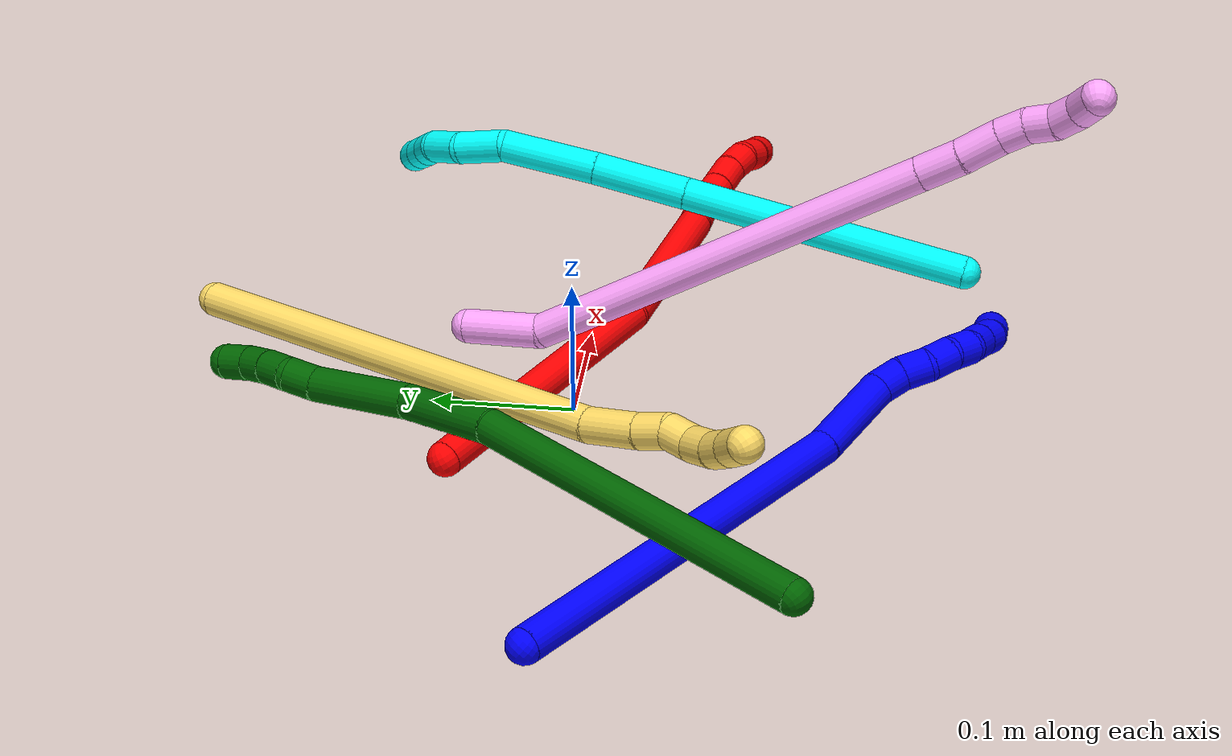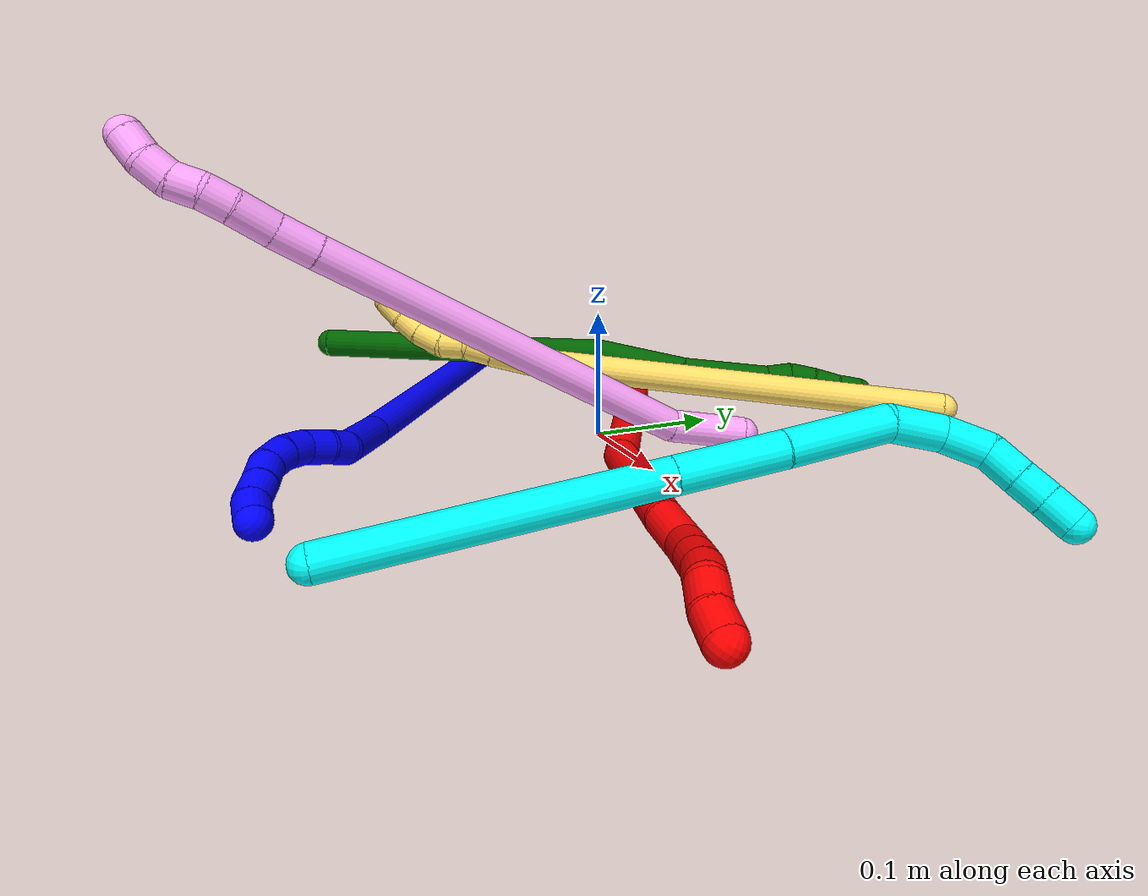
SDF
<sdf version="1.7">
 <world name="default">
  <plugin name="TubeGeneratorPlugin" filename="libtube_generator_plugin.so"/>
  <model name="photoneo_s_sensor">
   <static>1</static>
   <pose>0 0 2 1.57079 1.57079 3.14159</pose>
   <link name="link">
    <inertial><mass>0.1</mass></inertial>
    <sensor name="sensor" type="depth">
     <update_rate>30</update_rate>
     <camera>
      <horizontal_fov>1.22</horizontal_fov>
      <image><width>1920</width><height>1200</height><format>B8G8R8</format></image>
      <clip><near>0.1</near><far>4</far></clip>
      <depth_camera><output>points</output></depth_camera>
     </camera>
     <plugin name="camera_plugin" filename="libgazebo_ros_depth_camera.so">
      <baseline>0.2</baseline>
      <alwaysOn>1</alwaysOn>
      <updateRate>0.0</updateRate>
      <cameraName>camera_ir</cameraName>
      <imageTopicName>/camera/color/image_raw</imageTopicName>
      <cameraInfoTopicName>/camera/color/camera_info</cameraInfoTopicName>
      <depthImageTopicName>/camera/depth/image_raw</depthImageTopicName>
      <depthImageCameraInfoTopicName>/camera/depth/camera_info</depthImageCameraInfoTopicName>
      <pointCloudTopicName>/camera/depth/points</pointCloudTopicName>
      <frameName>fr_optical</frameName>
      <pointCloudCutoff>0.1</pointCloudCutoff>
      <pointCloudCutoffMax>2.0</pointCloudCutoffMax>
      <distortionK1>0</distortionK1>
      <distortionK2>0</distortionK2>
      <distortionK3>0</distortionK3>
      <distortionT1>0</distortionT1>
      <distortionT2>0</distortionT2>
      <CxPrime>0</CxPrime>
      <Cx>0</Cx>
      <Cy>0</Cy>
      <focalLength>0</focalLength>
      <hackBaseline>0</hackBaseline>
     </plugin>
    </sensor>
   </link>
  </model>
  <gravity>0 0 -9.8</gravity>
  <magnetic_field>6e-06 2.3e-05 -4.2e-05</magnetic_field>
  <atmosphere type="adiabatic"/>
  <physics name="default_physics" default="0" type="ode">
   <max_step_size>0.003</max_step_size>
   <real_time_factor>1</real_time_factor>
   <real_time_update_rate>1000</real_time_update_rate>
   <max_contacts>10000</max_contacts>
   <ode>
    <solver>
     <type>quick</type>
     <iters>100</iters>
     <sor>1.3</sor>
     <use_dynamic_moi_rescaling>0</use_dynamic_moi_rescaling>
    </solver>
    <constraints>
     <contact_max_correcting_vel>0</contact_max_correcting_vel>
     <contact_surface_layer>0.001</contact_surface_layer>
     <cfm>0</cfm>
     <erp>0.2</erp>
    </constraints>
   </ode>
  </physics>
  <scene><ambient>0.4 0.4 0.4 1</ambient><background>0.7 0.7 0.7 1</background><shadows>0</shadows></scene>
  <audio><device>default</device></audio>
  <spherical_coordinates>
   <surface_model>EARTH_WGS84</surface_model>
   <latitude_deg>0</latitude_deg>
   <longitude_deg>0</longitude_deg>
   <elevation>0</elevation>
   <heading_deg>0</heading_deg>
  </spherical_coordinates>
  <model name="bin">
   <static>1</static>
   <link name="bottom">
    <collision name="collision-bottom">
     <pose>0 0 -0.01 0 -0 0</pose>
     <geometry><box><size>0.8 0.6 0.02</size></box></geometry>
     <surface>
      <friction><ode><mu>100</mu><mu2>100</mu2></ode></friction>
      <contact><collide_bitmask>65535</collide_bitmask></contact>
     </surface>
    </collision>
   </link>
   <link name="west_wall">
    <collision name="collision-west_wall">
     <pose>-0.41 0 0.1 0 -0 0</pose>
     <geometry><box><size>0.02 0.6 0.2</size></box></geometry>
     <surface>
      <friction><ode><mu>100</mu><mu2>100</mu2></ode></friction>
      <contact><collide_bitmask>65535</collide_bitmask></contact>
     </surface>
    </collision>
   </link>
   <link name="east_wall">
    <collision name="collision-east_wall">
     <pose>0.41 0 0.1 0 -0 0</pose>
     <geometry><box><size>0.02 0.6 0.2</size></box></geometry>
     <surface>
      <friction><ode><mu>100</mu><mu2>100</mu2></ode></friction>
      <contact><collide_bitmask>65535</collide_bitmask></contact>
     </surface>
    </collision>
   </link>
   <link name="south_wall">
    <collision name="collision-south_wall">
     <pose>0 -0.31 0.1 0 -0 0</pose>
     <geometry><box><size>0.8 0.02 0.2</size></box></geometry>
     <surface>
      <friction><ode><mu>100</mu><mu2>100</mu2></ode></friction>
      <contact><collide_bitmask>65535</collide_bitmask></contact>
     </surface>
    </collision>
   </link>
   <link name="north_wall">
    <collision name="collision-north_wall">
     <pose>0 0.31 0.1 0 -0 0</pose>
     <geometry><box><size>0.8 0.02 0.2</size></box></geometry>
     <surface>
      <friction><ode><mu>100</mu><mu2>100</mu2></ode></friction>
      <contact><collide_bitmask>65535</collide_bitmask></contact>
     </surface>
    </collision>
   </link>
  </model>
  <model name="1">
   <static>0</static>
   <link name="1">
    <collision name="collision-cylinder-e_1_1_4">
     <pose>0.105713 -0.023299 -0.095323 2.90187 0.822584 2.60277</pose>
     <geometry><cylinder><radius>0.0125</radius><length>0.288475</length></cylinder></geometry>
     <surface>
      <friction><ode><mu>1.16</mu><mu2>1.16</mu2><slip1>0</slip1><slip2>0</slip2></ode></friction>
      <contact><ode><kp>1e+06</kp><kd>1</kd><max_vel>0</max_vel><min_depth>0.001</min_depth></ode></contact>
     </surface>
    </collision>
    <visual name="visual-cylinder-e_1_1_4">
     <pose>0.105713 -0.023299 -0.095323 2.90187 0.822584 2.60277</pose>
     <geometry><cylinder><radius>0.0125</radius><length>0.288475</length></cylinder></geometry>
     <material><ambient>0 0 1 1</ambient></material>
    </visual>
    <collision name="collision-cylinder-e_2_4_5">
     <pose>0.234466 -0.057752 -0.215594 2.72114 0.700489 2.08428</pose>
     <geometry><cylinder><radius>0.0125</radius><length>0.071491</length></cylinder></geometry>
     <surface>
      <friction><ode><mu>1.16</mu><mu2>1.16</mu2><slip1>0</slip1><slip2>0</slip2></ode></friction>
      <contact><ode><kp>1e+06</kp><kd>1</kd><max_vel>0</max_vel><min_depth>0.001</min_depth></ode></contact>
     </surface>
    </collision>
    <visual name="visual-cylinder-e_2_4_5">
     <pose>0.234466 -0.057752 -0.215594 2.72114 0.700489 2.08428</pose>
     <geometry><cylinder><radius>0.0125</radius><length>0.071491</length></cylinder></geometry>
     <material><ambient>0 0 1 1</ambient></material>
    </visual>
    <collision name="collision-cylinder-e_3_5_6">
     <pose>0.261924 -0.068195 -0.249502 -3.06228 0.456721 -2.8034</pose>
     <geometry><cylinder><radius>0.0125</radius><length>0.020028</length></cylinder></geometry>
     <surface>
      <friction><ode><mu>1.16</mu><mu2>1.16</mu2><slip1>0</slip1><slip2>0</slip2></ode></friction>
      <contact><ode><kp>1e+06</kp><kd>1</kd><max_vel>0</max_vel><min_depth>0.001</min_depth></ode></contact>
     </surface>
    </collision>
    <visual name="visual-cylinder-e_3_5_6">
     <pose>0.261924 -0.068195 -0.249502 -3.06228 0.456721 -2.8034</pose>
     <geometry><cylinder><radius>0.0125</radius><length>0.020028</length></cylinder></geometry>
     <material><ambient>0 0 1 1</ambient></material>
    </visual>
    <collision name="collision-cylinder-e_4_6_7">
     <pose>0.270888 -0.064438 -0.266832 -2.79275 0.472035 -1.87693</pose>
     <geometry><cylinder><radius>0.0125</radius><length>0.020003</length></cylinder></geometry>
     <surface>
      <friction><ode><mu>1.16</mu><mu2>1.16</mu2><slip1>0</slip1><slip2>0</slip2></ode></friction>
      <contact><ode><kp>1e+06</kp><kd>1</kd><max_vel>0</max_vel><min_depth>0.001</min_depth></ode></contact>
     </surface>
    </collision>
    <visual name="visual-cylinder-e_4_6_7">
     <pose>0.270888 -0.064438 -0.266832 -2.79275 0.472035 -1.87693</pose>
     <geometry><cylinder><radius>0.0125</radius><length>0.020003</length></cylinder></geometry>
     <material><ambient>0 0 1 1</ambient></material>
    </visual>
    <collision name="collision-cylinder-e_5_7_8">
     <pose>0.281805 -0.060933 -0.282899 -3.08183 0.690535 -2.97578</pose>
     <geometry><cylinder><radius>0.0125</radius><length>0.02</length></cylinder></geometry>
     <surface>
      <friction><ode><mu>1.16</mu><mu2>1.16</mu2><slip1>0</slip1><slip2>0</slip2></ode></friction>
      <contact><ode><kp>1e+06</kp><kd>1</kd><max_vel>0</max_vel><min_depth>0.001</min_depth></ode></contact>
     </surface>
    </collision>
    <visual name="visual-cylinder-e_5_7_8">
     <pose>0.281805 -0.060933 -0.282899 -3.08183 0.690535 -2.97578</pose>
     <geometry><cylinder><radius>0.0125</radius><length>0.02</length></cylinder></geometry>
     <material><ambient>0 0 1 1</ambient></material>
    </visual>
    <collision name="collision-cylinder-e_6_8_9">
     <pose>0.296319 -0.060786 -0.296389 3.08754 0.951743 3.03679</pose>
     <geometry><cylinder><radius>0.0125</radius><length>0.020002</length></cylinder></geometry>
     <surface>
      <friction><ode><mu>1.16</mu><mu2>1.16</mu2><slip1>0</slip1><slip2>0</slip2></ode></friction>
      <contact><ode><kp>1e+06</kp><kd>1</kd><max_vel>0</max_vel><min_depth>0.001</min_depth></ode></contact>
     </surface>
    </collision>
    <visual name="visual-cylinder-e_6_8_9">
     <pose>0.296319 -0.060786 -0.296389 3.08754 0.951743 3.03679</pose>
     <geometry><cylinder><radius>0.0125</radius><length>0.020002</length></cylinder></geometry>
     <material><ambient>0 0 1 1</ambient></material>
    </visual>
    <collision name="collision-cylinder-e_7_9_10">
     <pose>0.313298 -0.064225 -0.305677 2.41183 1.08288 2.00983</pose>
     <geometry><cylinder><radius>0.0125</radius><length>0.02</length></cylinder></geometry>
     <surface>
      <friction><ode><mu>1.16</mu><mu2>1.16</mu2><slip1>0</slip1><slip2>0</slip2></ode></friction>
      <contact><ode><kp>1e+06</kp><kd>1</kd><max_vel>0</max_vel><min_depth>0.001</min_depth></ode></contact>
     </surface>
    </collision>
    <visual name="visual-cylinder-e_7_9_10">
     <pose>0.313298 -0.064225 -0.305677 2.41183 1.08288 2.00983</pose>
     <geometry><cylinder><radius>0.0125</radius><length>0.02</length></cylinder></geometry>
     <material><ambient>0 0 1 1</ambient></material>
    </visual>
    <collision name="collision-cylinder-e_8_10_11">
     <pose>0.331128 -0.069825 -0.312769 2.53903 1.1189 2.22032</pose>
     <geometry><cylinder><radius>0.0125</radius><length>0.02</length></cylinder></geometry>
     <surface>
      <friction><ode><mu>1.16</mu><mu2>1.16</mu2><slip1>0</slip1><slip2>0</slip2></ode></friction>
      <contact><ode><kp>1e+06</kp><kd>1</kd><max_vel>0</max_vel><min_depth>0.001</min_depth></ode></contact>
     </surface>
    </collision>
    <visual name="visual-cylinder-e_8_10_11">
     <pose>0.331128 -0.069825 -0.312769 2.53903 1.1189 2.22032</pose>
     <geometry><cylinder><radius>0.0125</radius><length>0.02</length></cylinder></geometry>
     <material><ambient>0 0 1 1</ambient></material>
    </visual>
    <collision name="collision-cylinder-e_9_11_2">
     <pose>0.348244 -0.077812 -0.318287 1.90602 0.94759 1.25016</pose>
     <geometry><cylinder><radius>0.0125</radius><length>0.02</length></cylinder></geometry>
     <surface>
      <friction><ode><mu>1.16</mu><mu2>1.16</mu2><slip1>0</slip1><slip2>0</slip2></ode></friction>
      <contact><ode><kp>1e+06</kp><kd>1</kd><max_vel>0</max_vel><min_depth>0.001</min_depth></ode></contact>
     </surface>
    </collision>
    <visual name="visual-cylinder-e_9_11_2">
     <pose>0.348244 -0.077812 -0.318287 1.90602 0.94759 1.25016</pose>
     <geometry><cylinder><radius>0.0125</radius><length>0.02</length></cylinder></geometry>
     <material><ambient>0 0 1 1</ambient></material>
    </visual>
    <collision name="collision-sphere-2">
     <pose>0.356365 -0.083324 -0.320207 0 -0 0</pose>
     <geometry><sphere><radius>0.0125</radius></sphere></geometry>
     <surface>
      <friction><ode><mu>1.16</mu><mu2>1.16</mu2><slip1>0</slip1><slip2>0</slip2></ode></friction>
      <contact><ode><kp>1e+06</kp><kd>1</kd><max_vel>0</max_vel><min_depth>0.001</min_depth></ode></contact>
     </surface>
    </collision>
    <visual name="visual-sphere-2">
     <pose>0.356365 -0.083324 -0.320207 0 -0 0</pose>
     <geometry><sphere><radius>0.0125</radius></sphere></geometry>
     <material><ambient>0 0 1 1</ambient></material>
    </visual>
    <collision name="collision-sphere-11">
     <pose>0.340124 -0.0723 -0.316367 0 -0 0</pose>
     <geometry><sphere><radius>0.0125</radius></sphere></geometry>
     <surface>
      <friction><ode><mu>1.16</mu><mu2>1.16</mu2><slip1>0</slip1><slip2>0</slip2></ode></friction>
      <contact><ode><kp>1e+06</kp><kd>1</kd><max_vel>0</max_vel><min_depth>0.001</min_depth></ode></contact>
     </surface>
    </collision>
    <visual name="visual-sphere-11">
     <pose>0.340124 -0.0723 -0.316367 0 -0 0</pose>
     <geometry><sphere><radius>0.0125</radius></sphere></geometry>
     <material><ambient>0 0 1 1</ambient></material>
    </visual>
    <collision name="collision-sphere-10">
     <pose>0.322131 -0.06735 -0.309171 0 -0 0</pose>
     <geometry><sphere><radius>0.0125</radius></sphere></geometry>
     <surface>
      <friction><ode><mu>1.16</mu><mu2>1.16</mu2><slip1>0</slip1><slip2>0</slip2></ode></friction>
      <contact><ode><kp>1e+06</kp><kd>1</kd><max_vel>0</max_vel><min_depth>0.001</min_depth></ode></contact>
     </surface>
    </collision>
    <visual name="visual-sphere-10">
     <pose>0.322131 -0.06735 -0.309171 0 -0 0</pose>
     <geometry><sphere><radius>0.0125</radius></sphere></geometry>
     <material><ambient>0 0 1 1</ambient></material>
    </visual>
    <collision name="collision-sphere-9">
     <pose>0.304464 -0.0611 -0.302183 0 -0 0</pose>
     <geometry><sphere><radius>0.0125</radius></sphere></geometry>
     <surface>
      <friction><ode><mu>1.16</mu><mu2>1.16</mu2><slip1>0</slip1><slip2>0</slip2></ode></friction>
      <contact><ode><kp>1e+06</kp><kd>1</kd><max_vel>0</max_vel><min_depth>0.001</min_depth></ode></contact>
     </surface>
    </collision>
    <visual name="visual-sphere-9">
     <pose>0.304464 -0.0611 -0.302183 0 -0 0</pose>
     <geometry><sphere><radius>0.0125</radius></sphere></geometry>
     <material><ambient>0 0 1 1</ambient></material>
    </visual>
    <collision name="collision-sphere-4">
     <pose>0.211425 -0.046598 -0.190646 0 -0 0</pose>
     <geometry><sphere><radius>0.0125</radius></sphere></geometry>
     <surface>
      <friction><ode><mu>1.16</mu><mu2>1.16</mu2><slip1>0</slip1><slip2>0</slip2></ode></friction>
      <contact><ode><kp>1e+06</kp><kd>1</kd><max_vel>0</max_vel><min_depth>0.001</min_depth></ode></contact>
     </surface>
    </collision>
    <visual name="visual-sphere-4">
     <pose>0.211425 -0.046598 -0.190646 0 -0 0</pose>
     <geometry><sphere><radius>0.0125</radius></sphere></geometry>
     <material><ambient>0 0 1 1</ambient></material>
    </visual>
    <collision name="collision-sphere-1">
     <geometry><sphere><radius>0.0125</radius></sphere></geometry>
     <surface>
      <friction><ode><mu>1.16</mu><mu2>1.16</mu2><slip1>0</slip1><slip2>0</slip2></ode></friction>
      <contact><ode><kp>1e+06</kp><kd>1</kd><max_vel>0</max_vel><min_depth>0.001</min_depth></ode></contact>
     </surface>
    </collision>
    <visual name="visual-sphere-1">
     <geometry><sphere><radius>0.0125</radius></sphere></geometry>
     <material><ambient>0 0 1 1</ambient></material>
    </visual>
    <collision name="collision-sphere-8">
     <pose>0.288174 -0.060473 -0.290594 0 -0 0</pose>
     <geometry><sphere><radius>0.0125</radius></sphere></geometry>
     <surface>
      <friction><ode><mu>1.16</mu><mu2>1.16</mu2><slip1>0</slip1><slip2>0</slip2></ode></friction>
      <contact><ode><kp>1e+06</kp><kd>1</kd><max_vel>0</max_vel><min_depth>0.001</min_depth></ode></contact>
     </surface>
    </collision>
    <visual name="visual-sphere-8">
     <pose>0.288174 -0.060473 -0.290594 0 -0 0</pose>
     <geometry><sphere><radius>0.0125</radius></sphere></geometry>
     <material><ambient>0 0 1 1</ambient></material>
    </visual>
    <collision name="collision-sphere-5">
     <pose>0.257507 -0.068907 -0.240542 0 -0 0</pose>
     <geometry><sphere><radius>0.0125</radius></sphere></geometry>
     <surface>
      <friction><ode><mu>1.16</mu><mu2>1.16</mu2><slip1>0</slip1><slip2>0</slip2></ode></friction>
      <contact><ode><kp>1e+06</kp><kd>1</kd><max_vel>0</max_vel><min_depth>0.001</min_depth></ode></contact>
     </surface>
    </collision>
    <visual name="visual-sphere-5">
     <pose>0.257507 -0.068907 -0.240542 0 -0 0</pose>
     <geometry><sphere><radius>0.0125</radius></sphere></geometry>
     <material><ambient>0 0 1 1</ambient></material>
    </visual>
    <collision name="collision-sphere-6">
     <pose>0.26634 -0.067483 -0.258461 0 -0 0</pose>
     <geometry><sphere><radius>0.0125</radius></sphere></geometry>
     <surface>
      <friction><ode><mu>1.16</mu><mu2>1.16</mu2><slip1>0</slip1><slip2>0</slip2></ode></friction>
      <contact><ode><kp>1e+06</kp><kd>1</kd><max_vel>0</max_vel><min_depth>0.001</min_depth></ode></contact>
     </surface>
    </collision>
    <visual name="visual-sphere-6">
     <pose>0.26634 -0.067483 -0.258461 0 -0 0</pose>
     <geometry><sphere><radius>0.0125</radius></sphere></geometry>
     <material><ambient>0 0 1 1</ambient></material>
    </visual>
    <collision name="collision-sphere-7">
     <pose>0.275435 -0.061393 -0.275203 0 -0 0</pose>
     <geometry><sphere><radius>0.0125</radius></sphere></geometry>
     <surface>
      <friction><ode><mu>1.16</mu><mu2>1.16</mu2><slip1>0</slip1><slip2>0</slip2></ode></friction>
      <contact><ode><kp>1e+06</kp><kd>1</kd><max_vel>0</max_vel><min_depth>0.001</min_depth></ode></contact>
     </surface>
    </collision>
    <visual name="visual-sphere-7">
     <pose>0.275435 -0.061393 -0.275203 0 -0 0</pose>
     <geometry><sphere><radius>0.0125</radius></sphere></geometry>
     <material><ambient>0 0 1 1</ambient></material>
    </visual>
    <inertial>
     <pose>0.178678 -0.040353 -0.167134 0 -0 0</pose>
     <mass>0.5</mass>
     <inertia>
      <ixx>-0.000439</ixx>
      <ixy>0</ixy>
      <ixz>0</ixz>
      <iyy>0.002606</iyy>
      <iyz>0</iyz>
      <izz>-0.001192</izz>
     </inertia>
    </inertial>
   </link>
   <pose>-0.275614 -0.008357 0.0115 -2.81852 0.743633 -0.566054</pose>
  </model>
  <model name="2">
   <static>0</static>
   <link name="2">
    <collision name="collision-cylinder-e_1_1_4">
     <pose>0.096341 -0.050502 -0.005116 1.67175 1.08587 1.17736</pose>
     <geometry><cylinder><radius>0.0125</radius><length>0.217791</length></cylinder></geometry>
     <surface>
      <friction><ode><mu>1.16</mu><mu2>1.16</mu2><slip1>0</slip1><slip2>0</slip2></ode></friction>
      <contact><ode><kp>1e+06</kp><kd>1</kd><max_vel>0</max_vel><min_depth>0.001</min_depth></ode></contact>
     </surface>
    </collision>
    <visual name="visual-cylinder-e_1_1_4">
     <pose>0.096341 -0.050502 -0.005116 1.67175 1.08587 1.17736</pose>
     <geometry><cylinder><radius>0.0125</radius><length>0.217791</length></cylinder></geometry>
     <material><ambient>1 0 0 1</ambient></material>
    </visual>
    <collision name="collision-cylinder-e_2_4_5">
     <pose>0.257095 -0.119188 -0.003882 1.23485 1.28024 0.972813</pose>
     <geometry><cylinder><radius>0.0125</radius><length>0.134462</length></cylinder></geometry>
     <surface>
      <friction><ode><mu>1.16</mu><mu2>1.16</mu2><slip1>0</slip1><slip2>0</slip2></ode></friction>
      <contact><ode><kp>1e+06</kp><kd>1</kd><max_vel>0</max_vel><min_depth>0.001</min_depth></ode></contact>
     </surface>
    </collision>
    <visual name="visual-cylinder-e_2_4_5">
     <pose>0.257095 -0.119188 -0.003882 1.23485 1.28024 0.972813</pose>
     <geometry><cylinder><radius>0.0125</radius><length>0.134462</length></cylinder></geometry>
     <material><ambient>1 0 0 1</ambient></material>
    </visual>
    <collision name="collision-cylinder-e_3_5_6">
     <pose>0.337507 -0.137919 0.003184 0.651948 1.51451 0.618539</pose>
     <geometry><cylinder><radius>0.0125</radius><length>0.032048</length></cylinder></geometry>
     <surface>
      <friction><ode><mu>1.16</mu><mu2>1.16</mu2><slip1>0</slip1><slip2>0</slip2></ode></friction>
      <contact><ode><kp>1e+06</kp><kd>1</kd><max_vel>0</max_vel><min_depth>0.001</min_depth></ode></contact>
     </surface>
    </collision>
    <visual name="visual-cylinder-e_3_5_6">
     <pose>0.337507 -0.137919 0.003184 0.651948 1.51451 0.618539</pose>
     <geometry><cylinder><radius>0.0125</radius><length>0.032048</length></cylinder></geometry>
     <material><ambient>1 0 0 1</ambient></material>
    </visual>
    <collision name="collision-cylinder-e_4_6_7">
     <pose>0.367316 -0.144819 0.006475 1.18573 1.11007 0.791404</pose>
     <geometry><cylinder><radius>0.0125</radius><length>0.030836</length></cylinder></geometry>
     <surface>
      <friction><ode><mu>1.16</mu><mu2>1.16</mu2><slip1>0</slip1><slip2>0</slip2></ode></friction>
      <contact><ode><kp>1e+06</kp><kd>1</kd><max_vel>0</max_vel><min_depth>0.001</min_depth></ode></contact>
     </surface>
    </collision>
    <visual name="visual-cylinder-e_4_6_7">
     <pose>0.367316 -0.144819 0.006475 1.18573 1.11007 0.791404</pose>
     <geometry><cylinder><radius>0.0125</radius><length>0.030836</length></cylinder></geometry>
     <material><ambient>1 0 0 1</ambient></material>
    </visual>
    <collision name="collision-cylinder-e_5_7_8">
     <pose>0.39189 -0.155709 0.010844 1.1943 1.14522 0.826236</pose>
     <geometry><cylinder><radius>0.0125</radius><length>0.023635</length></cylinder></geometry>
     <surface>
      <friction><ode><mu>1.16</mu><mu2>1.16</mu2><slip1>0</slip1><slip2>0</slip2></ode></friction>
      <contact><ode><kp>1e+06</kp><kd>1</kd><max_vel>0</max_vel><min_depth>0.001</min_depth></ode></contact>
     </surface>
    </collision>
    <visual name="visual-cylinder-e_5_7_8">
     <pose>0.39189 -0.155709 0.010844 1.1943 1.14522 0.826236</pose>
     <geometry><cylinder><radius>0.0125</radius><length>0.023635</length></cylinder></geometry>
     <material><ambient>1 0 0 1</ambient></material>
    </visual>
    <collision name="collision-cylinder-e_6_8_9">
     <pose>0.412083 -0.164793 0.012913 1.51021 1.12075 1.0669</pose>
     <geometry><cylinder><radius>0.0125</radius><length>0.020944</length></cylinder></geometry>
     <surface>
      <friction><ode><mu>1.16</mu><mu2>1.16</mu2><slip1>0</slip1><slip2>0</slip2></ode></friction>
      <contact><ode><kp>1e+06</kp><kd>1</kd><max_vel>0</max_vel><min_depth>0.001</min_depth></ode></contact>
     </surface>
    </collision>
    <visual name="visual-cylinder-e_6_8_9">
     <pose>0.412083 -0.164793 0.012913 1.51021 1.12075 1.0669</pose>
     <geometry><cylinder><radius>0.0125</radius><length>0.020944</length></cylinder></geometry>
     <material><ambient>1 0 0 1</ambient></material>
    </visual>
    <collision name="collision-cylinder-e_7_9_10">
     <pose>0.431008 -0.171126 0.010468 2.56062 1.24058 2.34891</pose>
     <geometry><cylinder><radius>0.0125</radius><length>0.020075</length></cylinder></geometry>
     <surface>
      <friction><ode><mu>1.16</mu><mu2>1.16</mu2><slip1>0</slip1><slip2>0</slip2></ode></friction>
      <contact><ode><kp>1e+06</kp><kd>1</kd><max_vel>0</max_vel><min_depth>0.001</min_depth></ode></contact>
     </surface>
    </collision>
    <visual name="visual-cylinder-e_7_9_10">
     <pose>0.431008 -0.171126 0.010468 2.56062 1.24058 2.34891</pose>
     <geometry><cylinder><radius>0.0125</radius><length>0.020075</length></cylinder></geometry>
     <material><ambient>1 0 0 1</ambient></material>
    </visual>
    <collision name="collision-cylinder-e_8_10_2">
     <pose>0.450437 -0.172633 0.005922 -2.9898 1.38699 -2.95913</pose>
     <geometry><cylinder><radius>0.0125</radius><length>0.020208</length></cylinder></geometry>
     <surface>
      <friction><ode><mu>1.16</mu><mu2>1.16</mu2><slip1>0</slip1><slip2>0</slip2></ode></friction>
      <contact><ode><kp>1e+06</kp><kd>1</kd><max_vel>0</max_vel><min_depth>0.001</min_depth></ode></contact>
     </surface>
    </collision>
    <visual name="visual-cylinder-e_8_10_2">
     <pose>0.450437 -0.172633 0.005922 -2.9898 1.38699 -2.95913</pose>
     <geometry><cylinder><radius>0.0125</radius><length>0.020208</length></cylinder></geometry>
     <material><ambient>1 0 0 1</ambient></material>
    </visual>
    <collision name="collision-sphere-2">
     <pose>0.46037 -0.172354 0.004097 0 -0 0</pose>
     <geometry><sphere><radius>0.0125</radius></sphere></geometry>
     <surface>
      <friction><ode><mu>1.16</mu><mu2>1.16</mu2><slip1>0</slip1><slip2>0</slip2></ode></friction>
      <contact><ode><kp>1e+06</kp><kd>1</kd><max_vel>0</max_vel><min_depth>0.001</min_depth></ode></contact>
     </surface>
    </collision>
    <visual name="visual-sphere-2">
     <pose>0.46037 -0.172354 0.004097 0 -0 0</pose>
     <geometry><sphere><radius>0.0125</radius></sphere></geometry>
     <material><ambient>1 0 0 1</ambient></material>
    </visual>
    <collision name="collision-sphere-10">
     <pose>0.440503 -0.172913 0.007748 0 -0 0</pose>
     <geometry><sphere><radius>0.0125</radius></sphere></geometry>
     <surface>
      <friction><ode><mu>1.16</mu><mu2>1.16</mu2><slip1>0</slip1><slip2>0</slip2></ode></friction>
      <contact><ode><kp>1e+06</kp><kd>1</kd><max_vel>0</max_vel><min_depth>0.001</min_depth></ode></contact>
     </surface>
    </collision>
    <visual name="visual-sphere-10">
     <pose>0.440503 -0.172913 0.007748 0 -0 0</pose>
     <geometry><sphere><radius>0.0125</radius></sphere></geometry>
     <material><ambient>1 0 0 1</ambient></material>
    </visual>
    <collision name="collision-sphere-9">
     <pose>0.421512 -0.16934 0.013189 0 -0 0</pose>
     <geometry><sphere><radius>0.0125</radius></sphere></geometry>
     <surface>
      <friction><ode><mu>1.16</mu><mu2>1.16</mu2><slip1>0</slip1><slip2>0</slip2></ode></friction>
      <contact><ode><kp>1e+06</kp><kd>1</kd><max_vel>0</max_vel><min_depth>0.001</min_depth></ode></contact>
     </surface>
    </collision>
    <visual name="visual-sphere-9">
     <pose>0.421512 -0.16934 0.013189 0 -0 0</pose>
     <geometry><sphere><radius>0.0125</radius></sphere></geometry>
     <material><ambient>1 0 0 1</ambient></material>
    </visual>
    <collision name="collision-sphere-4">
     <pose>0.192682 -0.101004 -0.010232 0 -0 0</pose>
     <geometry><sphere><radius>0.0125</radius></sphere></geometry>
     <surface>
      <friction><ode><mu>1.16</mu><mu2>1.16</mu2><slip1>0</slip1><slip2>0</slip2></ode></friction>
      <contact><ode><kp>1e+06</kp><kd>1</kd><max_vel>0</max_vel><min_depth>0.001</min_depth></ode></contact>
     </surface>
    </collision>
    <visual name="visual-sphere-4">
     <pose>0.192682 -0.101004 -0.010232 0 -0 0</pose>
     <geometry><sphere><radius>0.0125</radius></sphere></geometry>
     <material><ambient>1 0 0 1</ambient></material>
    </visual>
    <collision name="collision-sphere-1">
     <geometry><sphere><radius>0.0125</radius></sphere></geometry>
     <surface>
      <friction><ode><mu>1.16</mu><mu2>1.16</mu2><slip1>0</slip1><slip2>0</slip2></ode></friction>
      <contact><ode><kp>1e+06</kp><kd>1</kd><max_vel>0</max_vel><min_depth>0.001</min_depth></ode></contact>
     </surface>
    </collision>
    <visual name="visual-sphere-1">
     <geometry><sphere><radius>0.0125</radius></sphere></geometry>
     <material><ambient>1 0 0 1</ambient></material>
    </visual>
    <collision name="collision-sphere-8">
     <pose>0.402653 -0.160246 0.012637 0 -0 0</pose>
     <geometry><sphere><radius>0.0125</radius></sphere></geometry>
     <surface>
      <friction><ode><mu>1.16</mu><mu2>1.16</mu2><slip1>0</slip1><slip2>0</slip2></ode></friction>
      <contact><ode><kp>1e+06</kp><kd>1</kd><max_vel>0</max_vel><min_depth>0.001</min_depth></ode></contact>
     </surface>
    </collision>
    <visual name="visual-sphere-8">
     <pose>0.402653 -0.160246 0.012637 0 -0 0</pose>
     <geometry><sphere><radius>0.0125</radius></sphere></geometry>
     <material><ambient>1 0 0 1</ambient></material>
    </visual>
    <collision name="collision-sphere-5">
     <pose>0.321509 -0.137372 0.002467 0 -0 0</pose>
     <geometry><sphere><radius>0.0125</radius></sphere></geometry>
     <surface>
      <friction><ode><mu>1.16</mu><mu2>1.16</mu2><slip1>0</slip1><slip2>0</slip2></ode></friction>
      <contact><ode><kp>1e+06</kp><kd>1</kd><max_vel>0</max_vel><min_depth>0.001</min_depth></ode></contact>
     </surface>
    </collision>
    <visual name="visual-sphere-5">
     <pose>0.321509 -0.137372 0.002467 0 -0 0</pose>
     <geometry><sphere><radius>0.0125</radius></sphere></geometry>
     <material><ambient>1 0 0 1</ambient></material>
    </visual>
    <collision name="collision-sphere-6">
     <pose>0.353506 -0.138466 0.0039 0 -0 0</pose>
     <geometry><sphere><radius>0.0125</radius></sphere></geometry>
     <surface>
      <friction><ode><mu>1.16</mu><mu2>1.16</mu2><slip1>0</slip1><slip2>0</slip2></ode></friction>
      <contact><ode><kp>1e+06</kp><kd>1</kd><max_vel>0</max_vel><min_depth>0.001</min_depth></ode></contact>
     </surface>
    </collision>
    <visual name="visual-sphere-6">
     <pose>0.353506 -0.138466 0.0039 0 -0 0</pose>
     <geometry><sphere><radius>0.0125</radius></sphere></geometry>
     <material><ambient>1 0 0 1</ambient></material>
    </visual>
    <collision name="collision-sphere-7">
     <pose>0.381127 -0.151172 0.00905 0 -0 0</pose>
     <geometry><sphere><radius>0.0125</radius></sphere></geometry>
     <surface>
      <friction><ode><mu>1.16</mu><mu2>1.16</mu2><slip1>0</slip1><slip2>0</slip2></ode></friction>
      <contact><ode><kp>1e+06</kp><kd>1</kd><max_vel>0</max_vel><min_depth>0.001</min_depth></ode></contact>
     </surface>
    </collision>
    <visual name="visual-sphere-7">
     <pose>0.381127 -0.151172 0.00905 0 -0 0</pose>
     <geometry><sphere><radius>0.0125</radius></sphere></geometry>
     <material><ambient>1 0 0 1</ambient></material>
    </visual>
    <inertial>
     <pose>0.226686 -0.099933 -0.000956 0 -0 0</pose>
     <mass>0.5</mass>
     <inertia>
      <ixx>0.000653</ixx>
      <ixy>0</ixy>
      <ixz>0</ixz>
      <iyy>0.001293</iyy>
      <iyz>0</iyz>
      <izz>-0.000519</izz>
     </inertia>
    </inertial>
   </link>
   <pose>-0.085675 0.074913 0.011493 -0.549428 0.200368 -0.063054</pose>
  </model>
  <model name="3">
   <static>0</static>
   <link name="3">
    <collision name="collision-cylinder-e_1_1_4">
     <pose>0.070986 0.05967 -0.058057 -2.3425 0.706034 -1.43491</pose>
     <geometry><cylinder><radius>0.0125</radius><length>0.218817</length></cylinder></geometry>
     <surface>
      <friction><ode><mu>1.16</mu><mu2>1.16</mu2><slip1>0</slip1><slip2>0</slip2></ode></friction>
      <contact><ode><kp>1e+06</kp><kd>1</kd><max_vel>0</max_vel><min_depth>0.001</min_depth></ode></contact>
     </surface>
    </collision>
    <visual name="visual-cylinder-e_1_1_4">
     <pose>0.070986 0.05967 -0.058057 -2.3425 0.706034 -1.43491</pose>
     <geometry><cylinder><radius>0.0125</radius><length>0.218817</length></cylinder></geometry>
     <material><ambient>0.003922 1 0.996078 1</ambient></material>
    </visual>
    <collision name="collision-cylinder-e_2_4_5">
     <pose>0.1655 0.139206 -0.135211 -2.33642 0.706686 -1.42752</pose>
     <geometry><cylinder><radius>0.0125</radius><length>0.072468</length></cylinder></geometry>
     <surface>
      <friction><ode><mu>1.16</mu><mu2>1.16</mu2><slip1>0</slip1><slip2>0</slip2></ode></friction>
      <contact><ode><kp>1e+06</kp><kd>1</kd><max_vel>0</max_vel><min_depth>0.001</min_depth></ode></contact>
     </surface>
    </collision>
    <visual name="visual-cylinder-e_2_4_5">
     <pose>0.1655 0.139206 -0.135211 -2.33642 0.706686 -1.42752</pose>
     <geometry><cylinder><radius>0.0125</radius><length>0.072468</length></cylinder></geometry>
     <material><ambient>0.003922 1 0.996078 1</ambient></material>
    </visual>
    <collision name="collision-cylinder-e_3_5_6">
     <pose>0.213237 0.179994 -0.172021 -2.27336 0.723434 -1.36899</pose>
     <geometry><cylinder><radius>0.0125</radius><length>0.073146</length></cylinder></geometry>
     <surface>
      <friction><ode><mu>1.16</mu><mu2>1.16</mu2><slip1>0</slip1><slip2>0</slip2></ode></friction>
      <contact><ode><kp>1e+06</kp><kd>1</kd><max_vel>0</max_vel><min_depth>0.001</min_depth></ode></contact>
     </surface>
    </collision>
    <visual name="visual-cylinder-e_3_5_6">
     <pose>0.213237 0.179994 -0.172021 -2.27336 0.723434 -1.36899</pose>
     <geometry><cylinder><radius>0.0125</radius><length>0.073146</length></cylinder></geometry>
     <material><ambient>0.003922 1 0.996078 1</ambient></material>
    </visual>
    <collision name="collision-cylinder-e_4_6_7">
     <pose>0.243289 0.214977 -0.20083 -2.23884 0.315276 -0.633726</pose>
     <geometry><cylinder><radius>0.0125</radius><length>0.037682</length></cylinder></geometry>
     <surface>
      <friction><ode><mu>1.16</mu><mu2>1.16</mu2><slip1>0</slip1><slip2>0</slip2></ode></friction>
      <contact><ode><kp>1e+06</kp><kd>1</kd><max_vel>0</max_vel><min_depth>0.001</min_depth></ode></contact>
     </surface>
    </collision>
    <visual name="visual-cylinder-e_4_6_7">
     <pose>0.243289 0.214977 -0.20083 -2.23884 0.315276 -0.633726</pose>
     <geometry><cylinder><radius>0.0125</radius><length>0.037682</length></cylinder></geometry>
     <material><ambient>0.003922 1 0.996078 1</ambient></material>
    </visual>
    <collision name="collision-cylinder-e_5_7_8">
     <pose>0.250057 0.237802 -0.224822 -2.54476 0.059291 -0.192216</pose>
     <geometry><cylinder><radius>0.0125</radius><length>0.03124</length></cylinder></geometry>
     <surface>
      <friction><ode><mu>1.16</mu><mu2>1.16</mu2><slip1>0</slip1><slip2>0</slip2></ode></friction>
      <contact><ode><kp>1e+06</kp><kd>1</kd><max_vel>0</max_vel><min_depth>0.001</min_depth></ode></contact>
     </surface>
    </collision>
    <visual name="visual-cylinder-e_5_7_8">
     <pose>0.250057 0.237802 -0.224822 -2.54476 0.059291 -0.192216</pose>
     <geometry><cylinder><radius>0.0125</radius><length>0.03124</length></cylinder></geometry>
     <material><ambient>0.003922 1 0.996078 1</ambient></material>
    </visual>
    <collision name="collision-cylinder-e_6_8_9">
     <pose>0.246451 0.251348 -0.247832 -2.69986 -0.384951 1.42969</pose>
     <geometry><cylinder><radius>0.0125</radius><length>0.024138</length></cylinder></geometry>
     <surface>
      <friction><ode><mu>1.16</mu><mu2>1.16</mu2><slip1>0</slip1><slip2>0</slip2></ode></friction>
      <contact><ode><kp>1e+06</kp><kd>1</kd><max_vel>0</max_vel><min_depth>0.001</min_depth></ode></contact>
     </surface>
    </collision>
    <visual name="visual-cylinder-e_6_8_9">
     <pose>0.246451 0.251348 -0.247832 -2.69986 -0.384951 1.42969</pose>
     <geometry><cylinder><radius>0.0125</radius><length>0.024138</length></cylinder></geometry>
     <material><ambient>0.003922 1 0.996078 1</ambient></material>
    </visual>
    <collision name="collision-cylinder-e_7_9_10">
     <pose>0.238417 0.260737 -0.266527 -2.64895 -0.345004 1.212</pose>
     <geometry><cylinder><radius>0.0125</radius><length>0.020703</length></cylinder></geometry>
     <surface>
      <friction><ode><mu>1.16</mu><mu2>1.16</mu2><slip1>0</slip1><slip2>0</slip2></ode></friction>
      <contact><ode><kp>1e+06</kp><kd>1</kd><max_vel>0</max_vel><min_depth>0.001</min_depth></ode></contact>
     </surface>
    </collision>
    <visual name="visual-cylinder-e_7_9_10">
     <pose>0.238417 0.260737 -0.266527 -2.64895 -0.345004 1.212</pose>
     <geometry><cylinder><radius>0.0125</radius><length>0.020703</length></cylinder></geometry>
     <material><ambient>0.003922 1 0.996078 1</ambient></material>
    </visual>
    <collision name="collision-cylinder-e_8_10_2">
     <pose>0.230844 0.26966 -0.284257 -2.70077 -0.382791 1.42609</pose>
     <geometry><cylinder><radius>0.0125</radius><length>0.021806</length></cylinder></geometry>
     <surface>
      <friction><ode><mu>1.16</mu><mu2>1.16</mu2><slip1>0</slip1><slip2>0</slip2></ode></friction>
      <contact><ode><kp>1e+06</kp><kd>1</kd><max_vel>0</max_vel><min_depth>0.001</min_depth></ode></contact>
     </surface>
    </collision>
    <visual name="visual-cylinder-e_8_10_2">
     <pose>0.230844 0.26966 -0.284257 -2.70077 -0.382791 1.42609</pose>
     <geometry><cylinder><radius>0.0125</radius><length>0.021806</length></cylinder></geometry>
     <material><ambient>0.003922 1 0.996078 1</ambient></material>
    </visual>
    <collision name="collision-sphere-2">
     <pose>0.226772 0.273975 -0.293405 0 -0 0</pose>
     <geometry><sphere><radius>0.0125</radius></sphere></geometry>
     <surface>
      <friction><ode><mu>1.16</mu><mu2>1.16</mu2><slip1>0</slip1><slip2>0</slip2></ode></friction>
      <contact><ode><kp>1e+06</kp><kd>1</kd><max_vel>0</max_vel><min_depth>0.001</min_depth></ode></contact>
     </surface>
    </collision>
    <visual name="visual-sphere-2">
     <pose>0.226772 0.273975 -0.293405 0 -0 0</pose>
     <geometry><sphere><radius>0.0125</radius></sphere></geometry>
     <material><ambient>0.003922 1 0.996078 1</ambient></material>
    </visual>
    <collision name="collision-sphere-10">
     <pose>0.234917 0.265344 -0.27511 0 -0 0</pose>
     <geometry><sphere><radius>0.0125</radius></sphere></geometry>
     <surface>
      <friction><ode><mu>1.16</mu><mu2>1.16</mu2><slip1>0</slip1><slip2>0</slip2></ode></friction>
      <contact><ode><kp>1e+06</kp><kd>1</kd><max_vel>0</max_vel><min_depth>0.001</min_depth></ode></contact>
     </surface>
    </collision>
    <visual name="visual-sphere-10">
     <pose>0.234917 0.265344 -0.27511 0 -0 0</pose>
     <geometry><sphere><radius>0.0125</radius></sphere></geometry>
     <material><ambient>0.003922 1 0.996078 1</ambient></material>
    </visual>
    <collision name="collision-sphere-9">
     <pose>0.241918 0.25613 -0.257944 0 -0 0</pose>
     <geometry><sphere><radius>0.0125</radius></sphere></geometry>
     <surface>
      <friction><ode><mu>1.16</mu><mu2>1.16</mu2><slip1>0</slip1><slip2>0</slip2></ode></friction>
      <contact><ode><kp>1e+06</kp><kd>1</kd><max_vel>0</max_vel><min_depth>0.001</min_depth></ode></contact>
     </surface>
    </collision>
    <visual name="visual-sphere-9">
     <pose>0.241918 0.25613 -0.257944 0 -0 0</pose>
     <geometry><sphere><radius>0.0125</radius></sphere></geometry>
     <material><ambient>0.003922 1 0.996078 1</ambient></material>
    </visual>
    <collision name="collision-sphere-4">
     <pose>0.141973 0.119339 -0.116115 0 -0 0</pose>
     <geometry><sphere><radius>0.0125</radius></sphere></geometry>
     <surface>
      <friction><ode><mu>1.16</mu><mu2>1.16</mu2><slip1>0</slip1><slip2>0</slip2></ode></friction>
      <contact><ode><kp>1e+06</kp><kd>1</kd><max_vel>0</max_vel><min_depth>0.001</min_depth></ode></contact>
     </surface>
    </collision>
    <visual name="visual-sphere-4">
     <pose>0.141973 0.119339 -0.116115 0 -0 0</pose>
     <geometry><sphere><radius>0.0125</radius></sphere></geometry>
     <material><ambient>0.003922 1 0.996078 1</ambient></material>
    </visual>
    <collision name="collision-sphere-1">
     <geometry><sphere><radius>0.0125</radius></sphere></geometry>
     <surface>
      <friction><ode><mu>1.16</mu><mu2>1.16</mu2><slip1>0</slip1><slip2>0</slip2></ode></friction>
      <contact><ode><kp>1e+06</kp><kd>1</kd><max_vel>0</max_vel><min_depth>0.001</min_depth></ode></contact>
     </surface>
    </collision>
    <visual name="visual-sphere-1">
     <geometry><sphere><radius>0.0125</radius></sphere></geometry>
     <material><ambient>0.003922 1 0.996078 1</ambient></material>
    </visual>
    <collision name="collision-sphere-8">
     <pose>0.250983 0.246566 -0.237719 0 -0 0</pose>
     <geometry><sphere><radius>0.0125</radius></sphere></geometry>
     <surface>
      <friction><ode><mu>1.16</mu><mu2>1.16</mu2><slip1>0</slip1><slip2>0</slip2></ode></friction>
      <contact><ode><kp>1e+06</kp><kd>1</kd><max_vel>0</max_vel><min_depth>0.001</min_depth></ode></contact>
     </surface>
    </collision>
    <visual name="visual-sphere-8">
     <pose>0.250983 0.246566 -0.237719 0 -0 0</pose>
     <geometry><sphere><radius>0.0125</radius></sphere></geometry>
     <material><ambient>0.003922 1 0.996078 1</ambient></material>
    </visual>
    <collision name="collision-sphere-5">
     <pose>0.189028 0.159073 -0.154307 0 -0 0</pose>
     <geometry><sphere><radius>0.0125</radius></sphere></geometry>
     <surface>
      <friction><ode><mu>1.16</mu><mu2>1.16</mu2><slip1>0</slip1><slip2>0</slip2></ode></friction>
      <contact><ode><kp>1e+06</kp><kd>1</kd><max_vel>0</max_vel><min_depth>0.001</min_depth></ode></contact>
     </surface>
    </collision>
    <visual name="visual-sphere-5">
     <pose>0.189028 0.159073 -0.154307 0 -0 0</pose>
     <geometry><sphere><radius>0.0125</radius></sphere></geometry>
     <material><ambient>0.003922 1 0.996078 1</ambient></material>
    </visual>
    <collision name="collision-sphere-6">
     <pose>0.237447 0.200915 -0.189734 0 -0 0</pose>
     <geometry><sphere><radius>0.0125</radius></sphere></geometry>
     <surface>
      <friction><ode><mu>1.16</mu><mu2>1.16</mu2><slip1>0</slip1><slip2>0</slip2></ode></friction>
      <contact><ode><kp>1e+06</kp><kd>1</kd><max_vel>0</max_vel><min_depth>0.001</min_depth></ode></contact>
     </surface>
    </collision>
    <visual name="visual-sphere-6">
     <pose>0.237447 0.200915 -0.189734 0 -0 0</pose>
     <geometry><sphere><radius>0.0125</radius></sphere></geometry>
     <material><ambient>0.003922 1 0.996078 1</ambient></material>
    </visual>
    <collision name="collision-sphere-7">
     <pose>0.249131 0.229039 -0.211925 0 -0 0</pose>
     <geometry><sphere><radius>0.0125</radius></sphere></geometry>
     <surface>
      <friction><ode><mu>1.16</mu><mu2>1.16</mu2><slip1>0</slip1><slip2>0</slip2></ode></friction>
      <contact><ode><kp>1e+06</kp><kd>1</kd><max_vel>0</max_vel><min_depth>0.001</min_depth></ode></contact>
     </surface>
    </collision>
    <visual name="visual-sphere-7">
     <pose>0.249131 0.229039 -0.211925 0 -0 0</pose>
     <geometry><sphere><radius>0.0125</radius></sphere></geometry>
     <material><ambient>0.003922 1 0.996078 1</ambient></material>
    </visual>
    <inertial>
     <pose>0.152044 0.138371 -0.13475 0 -0 0</pose>
     <mass>0.5</mass>
     <inertia>
      <ixx>-0.000589</ixx>
      <ixy>0</ixy>
      <ixz>0</ixz>
      <iyy>-0.000351</iyy>
      <iyz>0</iyz>
      <izz>-0.00117</izz>
     </inertia>
    </inertial>
   </link>
   <pose>0.200382 -0.267785 0.012821 -1.56604 -0.881204 1.96984</pose>
  </model>
  <model name="4">
   <static>0</static>
   <link name="4">
    <collision name="collision-cylinder-e_1_1_4">
     <pose>-0.000974 -0.027912 0.007723 1.30087 -0.033622 -0.025583</pose>
     <geometry><cylinder><radius>0.0125</radius><length>0.057954</length></cylinder></geometry>
     <surface>
      <friction><ode><mu>1.16</mu><mu2>1.16</mu2><slip1>0</slip1><slip2>0</slip2></ode></friction>
      <contact><ode><kp>1e+06</kp><kd>1</kd><max_vel>0</max_vel><min_depth>0.001</min_depth></ode></contact>
     </surface>
    </collision>
    <visual name="visual-cylinder-e_1_1_4">
     <pose>-0.000974 -0.027912 0.007723 1.30087 -0.033622 -0.025583</pose>
     <geometry><cylinder><radius>0.0125</radius><length>0.057954</length></cylinder></geometry>
     <material><ambient>1 0.65098 0.996078 1</ambient></material>
    </visual>
    <collision name="collision-cylinder-e_2_4_5">
     <pose>0.037535 -0.201176 0.009897 1.60895 0.265056 0.27524</pose>
     <geometry><cylinder><radius>0.0125</radius><length>0.301443</length></cylinder></geometry>
     <surface>
      <friction><ode><mu>1.16</mu><mu2>1.16</mu2><slip1>0</slip1><slip2>0</slip2></ode></friction>
      <contact><ode><kp>1e+06</kp><kd>1</kd><max_vel>0</max_vel><min_depth>0.001</min_depth></ode></contact>
     </surface>
    </collision>
    <visual name="visual-cylinder-e_2_4_5">
     <pose>0.037535 -0.201176 0.009897 1.60895 0.265056 0.27524</pose>
     <geometry><cylinder><radius>0.0125</radius><length>0.301443</length></cylinder></geometry>
     <material><ambient>1 0.65098 0.996078 1</ambient></material>
    </visual>
    <collision name="collision-cylinder-e_3_5_6">
     <pose>0.081348 -0.3612 0.004185 1.58196 0.286924 0.290101</pose>
     <geometry><cylinder><radius>0.0125</radius><length>0.030595</length></cylinder></geometry>
     <surface>
      <friction><ode><mu>1.16</mu><mu2>1.16</mu2><slip1>0</slip1><slip2>0</slip2></ode></friction>
      <contact><ode><kp>1e+06</kp><kd>1</kd><max_vel>0</max_vel><min_depth>0.001</min_depth></ode></contact>
     </surface>
    </collision>
    <visual name="visual-cylinder-e_3_5_6">
     <pose>0.081348 -0.3612 0.004185 1.58196 0.286924 0.290101</pose>
     <geometry><cylinder><radius>0.0125</radius><length>0.030595</length></cylinder></geometry>
     <material><ambient>1 0.65098 0.996078 1</ambient></material>
    </visual>
    <collision name="collision-cylinder-e_4_6_7">
     <pose>0.090301 -0.389982 0.002537 1.67559 0.314975 0.349169</pose>
     <geometry><cylinder><radius>0.0125</radius><length>0.029847</length></cylinder></geometry>
     <surface>
      <friction><ode><mu>1.16</mu><mu2>1.16</mu2><slip1>0</slip1><slip2>0</slip2></ode></friction>
      <contact><ode><kp>1e+06</kp><kd>1</kd><max_vel>0</max_vel><min_depth>0.001</min_depth></ode></contact>
     </surface>
    </collision>
    <visual name="visual-cylinder-e_4_6_7">
     <pose>0.090301 -0.389982 0.002537 1.67559 0.314975 0.349169</pose>
     <geometry><cylinder><radius>0.0125</radius><length>0.029847</length></cylinder></geometry>
     <material><ambient>1 0.65098 0.996078 1</ambient></material>
    </visual>
    <collision name="collision-cylinder-e_5_7_8">
     <pose>0.09785 -0.413668 0.001316 1.54331 0.296513 0.288587</pose>
     <geometry><cylinder><radius>0.0125</radius><length>0.020029</length></cylinder></geometry>
     <surface>
      <friction><ode><mu>1.16</mu><mu2>1.16</mu2><slip1>0</slip1><slip2>0</slip2></ode></friction>
      <contact><ode><kp>1e+06</kp><kd>1</kd><max_vel>0</max_vel><min_depth>0.001</min_depth></ode></contact>
     </surface>
    </collision>
    <visual name="visual-cylinder-e_5_7_8">
     <pose>0.09785 -0.413668 0.001316 1.54331 0.296513 0.288587</pose>
     <geometry><cylinder><radius>0.0125</radius><length>0.020029</length></cylinder></geometry>
     <material><ambient>1 0.65098 0.996078 1</ambient></material>
    </visual>
    <collision name="collision-cylinder-e_6_8_9">
     <pose>0.102484 -0.432784 0.004196 1.30309 0.170904 0.130472</pose>
     <geometry><cylinder><radius>0.0125</radius><length>0.020083</length></cylinder></geometry>
     <surface>
      <friction><ode><mu>1.16</mu><mu2>1.16</mu2><slip1>0</slip1><slip2>0</slip2></ode></friction>
      <contact><ode><kp>1e+06</kp><kd>1</kd><max_vel>0</max_vel><min_depth>0.001</min_depth></ode></contact>
     </surface>
    </collision>
    <visual name="visual-cylinder-e_6_8_9">
     <pose>0.102484 -0.432784 0.004196 1.30309 0.170904 0.130472</pose>
     <geometry><cylinder><radius>0.0125</radius><length>0.020083</length></cylinder></geometry>
     <material><ambient>1 0.65098 0.996078 1</ambient></material>
    </visual>
    <collision name="collision-cylinder-e_7_9_10">
     <pose>0.109281 -0.450655 0.009019 1.31197 0.533621 0.41471</pose>
     <geometry><cylinder><radius>0.0125</radius><length>0.020011</length></cylinder></geometry>
     <surface>
      <friction><ode><mu>1.16</mu><mu2>1.16</mu2><slip1>0</slip1><slip2>0</slip2></ode></friction>
      <contact><ode><kp>1e+06</kp><kd>1</kd><max_vel>0</max_vel><min_depth>0.001</min_depth></ode></contact>
     </surface>
    </collision>
    <visual name="visual-cylinder-e_7_9_10">
     <pose>0.109281 -0.450655 0.009019 1.31197 0.533621 0.41471</pose>
     <geometry><cylinder><radius>0.0125</radius><length>0.020011</length></cylinder></geometry>
     <material><ambient>1 0.65098 0.996078 1</ambient></material>
    </visual>
    <collision name="collision-cylinder-e_8_10_2">
     <pose>0.121194 -0.465209 0.015101 1.01381 0.749276 0.429949</pose>
     <geometry><cylinder><radius>0.0125</radius><length>0.020037</length></cylinder></geometry>
     <surface>
      <friction><ode><mu>1.16</mu><mu2>1.16</mu2><slip1>0</slip1><slip2>0</slip2></ode></friction>
      <contact><ode><kp>1e+06</kp><kd>1</kd><max_vel>0</max_vel><min_depth>0.001</min_depth></ode></contact>
     </surface>
    </collision>
    <visual name="visual-cylinder-e_8_10_2">
     <pose>0.121194 -0.465209 0.015101 1.01381 0.749276 0.429949</pose>
     <geometry><cylinder><radius>0.0125</radius><length>0.020037</length></cylinder></geometry>
     <material><ambient>1 0.65098 0.996078 1</ambient></material>
    </visual>
    <collision name="collision-sphere-2">
     <pose>0.128018 -0.471436 0.018979 0 -0 0</pose>
     <geometry><sphere><radius>0.0125</radius></sphere></geometry>
     <surface>
      <friction><ode><mu>1.16</mu><mu2>1.16</mu2><slip1>0</slip1><slip2>0</slip2></ode></friction>
      <contact><ode><kp>1e+06</kp><kd>1</kd><max_vel>0</max_vel><min_depth>0.001</min_depth></ode></contact>
     </surface>
    </collision>
    <visual name="visual-sphere-2">
     <pose>0.128018 -0.471436 0.018979 0 -0 0</pose>
     <geometry><sphere><radius>0.0125</radius></sphere></geometry>
     <material><ambient>1 0.65098 0.996078 1</ambient></material>
    </visual>
    <collision name="collision-sphere-10">
     <pose>0.114371 -0.458983 0.011223 0 -0 0</pose>
     <geometry><sphere><radius>0.0125</radius></sphere></geometry>
     <surface>
      <friction><ode><mu>1.16</mu><mu2>1.16</mu2><slip1>0</slip1><slip2>0</slip2></ode></friction>
      <contact><ode><kp>1e+06</kp><kd>1</kd><max_vel>0</max_vel><min_depth>0.001</min_depth></ode></contact>
     </surface>
    </collision>
    <visual name="visual-sphere-10">
     <pose>0.114371 -0.458983 0.011223 0 -0 0</pose>
     <geometry><sphere><radius>0.0125</radius></sphere></geometry>
     <material><ambient>1 0.65098 0.996078 1</ambient></material>
    </visual>
    <collision name="collision-sphere-9">
     <pose>0.104192 -0.442327 0.006814 0 -0 0</pose>
     <geometry><sphere><radius>0.0125</radius></sphere></geometry>
     <surface>
      <friction><ode><mu>1.16</mu><mu2>1.16</mu2><slip1>0</slip1><slip2>0</slip2></ode></friction>
      <contact><ode><kp>1e+06</kp><kd>1</kd><max_vel>0</max_vel><min_depth>0.001</min_depth></ode></contact>
     </surface>
    </collision>
    <visual name="visual-sphere-9">
     <pose>0.104192 -0.442327 0.006814 0 -0 0</pose>
     <geometry><sphere><radius>0.0125</radius></sphere></geometry>
     <material><ambient>1 0.65098 0.996078 1</ambient></material>
    </visual>
    <collision name="collision-sphere-4">
     <pose>-0.001948 -0.055824 0.015445 0 -0 0</pose>
     <geometry><sphere><radius>0.0125</radius></sphere></geometry>
     <surface>
      <friction><ode><mu>1.16</mu><mu2>1.16</mu2><slip1>0</slip1><slip2>0</slip2></ode></friction>
      <contact><ode><kp>1e+06</kp><kd>1</kd><max_vel>0</max_vel><min_depth>0.001</min_depth></ode></contact>
     </surface>
    </collision>
    <visual name="visual-sphere-4">
     <pose>-0.001948 -0.055824 0.015445 0 -0 0</pose>
     <geometry><sphere><radius>0.0125</radius></sphere></geometry>
     <material><ambient>1 0.65098 0.996078 1</ambient></material>
    </visual>
    <collision name="collision-sphere-1">
     <geometry><sphere><radius>0.0125</radius></sphere></geometry>
     <surface>
      <friction><ode><mu>1.16</mu><mu2>1.16</mu2><slip1>0</slip1><slip2>0</slip2></ode></friction>
      <contact><ode><kp>1e+06</kp><kd>1</kd><max_vel>0</max_vel><min_depth>0.001</min_depth></ode></contact>
     </surface>
    </collision>
    <visual name="visual-sphere-1">
     <geometry><sphere><radius>0.0125</radius></sphere></geometry>
     <material><ambient>1 0.65098 0.996078 1</ambient></material>
    </visual>
    <collision name="collision-sphere-8">
     <pose>0.100776 -0.423242 0.001579 0 -0 0</pose>
     <geometry><sphere><radius>0.0125</radius></sphere></geometry>
     <surface>
      <friction><ode><mu>1.16</mu><mu2>1.16</mu2><slip1>0</slip1><slip2>0</slip2></ode></friction>
      <contact><ode><kp>1e+06</kp><kd>1</kd><max_vel>0</max_vel><min_depth>0.001</min_depth></ode></contact>
     </surface>
    </collision>
    <visual name="visual-sphere-8">
     <pose>0.100776 -0.423242 0.001579 0 -0 0</pose>
     <geometry><sphere><radius>0.0125</radius></sphere></geometry>
     <material><ambient>1 0.65098 0.996078 1</ambient></material>
    </visual>
    <collision name="collision-sphere-5">
     <pose>0.077019 -0.346528 0.004348 0 -0 0</pose>
     <geometry><sphere><radius>0.0125</radius></sphere></geometry>
     <surface>
      <friction><ode><mu>1.16</mu><mu2>1.16</mu2><slip1>0</slip1><slip2>0</slip2></ode></friction>
      <contact><ode><kp>1e+06</kp><kd>1</kd><max_vel>0</max_vel><min_depth>0.001</min_depth></ode></contact>
     </surface>
    </collision>
    <visual name="visual-sphere-5">
     <pose>0.077019 -0.346528 0.004348 0 -0 0</pose>
     <geometry><sphere><radius>0.0125</radius></sphere></geometry>
     <material><ambient>1 0.65098 0.996078 1</ambient></material>
    </visual>
    <collision name="collision-sphere-6">
     <pose>0.085678 -0.375871 0.004021 0 -0 0</pose>
     <geometry><sphere><radius>0.0125</radius></sphere></geometry>
     <surface>
      <friction><ode><mu>1.16</mu><mu2>1.16</mu2><slip1>0</slip1><slip2>0</slip2></ode></friction>
      <contact><ode><kp>1e+06</kp><kd>1</kd><max_vel>0</max_vel><min_depth>0.001</min_depth></ode></contact>
     </surface>
    </collision>
    <visual name="visual-sphere-6">
     <pose>0.085678 -0.375871 0.004021 0 -0 0</pose>
     <geometry><sphere><radius>0.0125</radius></sphere></geometry>
     <material><ambient>1 0.65098 0.996078 1</ambient></material>
    </visual>
    <collision name="collision-sphere-7">
     <pose>0.094924 -0.404094 0.001052 0 -0 0</pose>
     <geometry><sphere><radius>0.0125</radius></sphere></geometry>
     <surface>
      <friction><ode><mu>1.16</mu><mu2>1.16</mu2><slip1>0</slip1><slip2>0</slip2></ode></friction>
      <contact><ode><kp>1e+06</kp><kd>1</kd><max_vel>0</max_vel><min_depth>0.001</min_depth></ode></contact>
     </surface>
    </collision>
    <visual name="visual-sphere-7">
     <pose>0.094924 -0.404094 0.001052 0 -0 0</pose>
     <geometry><sphere><radius>0.0125</radius></sphere></geometry>
     <material><ambient>1 0.65098 0.996078 1</ambient></material>
    </visual>
    <inertial>
     <pose>0.050151 -0.240537 0.008457 0 -0 0</pose>
     <mass>0.5</mass>
     <inertia>
      <ixx>0.002776</ixx>
      <ixy>0</ixy>
      <ixz>0</ixz>
      <iyy>0.000655</iyy>
      <iyz>0</iyz>
      <izz>0.001639</izz>
     </inertia>
    </inertial>
   </link>
   <pose>0.080755 0.087842 0.012498 -2.26265 -1.24405 2.29295</pose>
  </model>
  <model name="5">
   <static>0</static>
   <link name="5">
    <collision name="collision-cylinder-e_1_1_4">
     <pose>-0.132707 -0.103265 -0.045424 1.9852 -0.866246 -1.23291</pose>
     <geometry><cylinder><radius>0.0125</radius><length>0.348357</length></cylinder></geometry>
     <surface>
      <friction><ode><mu>1.16</mu><mu2>1.16</mu2><slip1>0</slip1><slip2>0</slip2></ode></friction>
      <contact><ode><kp>1e+06</kp><kd>1</kd><max_vel>0</max_vel><min_depth>0.001</min_depth></ode></contact>
     </surface>
    </collision>
    <visual name="visual-cylinder-e_1_1_4">
     <pose>-0.132707 -0.103265 -0.045424 1.9852 -0.866246 -1.23291</pose>
     <geometry><cylinder><radius>0.0125</radius><length>0.348357</length></cylinder></geometry>
     <material><ambient>1 0.858824 0.4 1</ambient></material>
    </visual>
    <collision name="collision-cylinder-e_2_4_5">
     <pose>-0.278627 -0.220212 -0.098134 2.06007 -0.705872 -1.10051</pose>
     <geometry><cylinder><radius>0.0125</radius><length>0.040738</length></cylinder></geometry>
     <surface>
      <friction><ode><mu>1.16</mu><mu2>1.16</mu2><slip1>0</slip1><slip2>0</slip2></ode></friction>
      <contact><ode><kp>1e+06</kp><kd>1</kd><max_vel>0</max_vel><min_depth>0.001</min_depth></ode></contact>
     </surface>
    </collision>
    <visual name="visual-cylinder-e_2_4_5">
     <pose>-0.278627 -0.220212 -0.098134 2.06007 -0.705872 -1.10051</pose>
     <geometry><cylinder><radius>0.0125</radius><length>0.040738</length></cylinder></geometry>
     <material><ambient>1 0.858824 0.4 1</ambient></material>
    </visual>
    <collision name="collision-cylinder-e_3_5_6">
     <pose>-0.298159 -0.241635 -0.110189 2.12302 -0.607395 -1.02282</pose>
     <geometry><cylinder><radius>0.0125</radius><length>0.022143</length></cylinder></geometry>
     <surface>
      <friction><ode><mu>1.16</mu><mu2>1.16</mu2><slip1>0</slip1><slip2>0</slip2></ode></friction>
      <contact><ode><kp>1e+06</kp><kd>1</kd><max_vel>0</max_vel><min_depth>0.001</min_depth></ode></contact>
     </surface>
    </collision>
    <visual name="visual-cylinder-e_3_5_6">
     <pose>-0.298159 -0.241635 -0.110189 2.12302 -0.607395 -1.02282</pose>
     <geometry><cylinder><radius>0.0125</radius><length>0.022143</length></cylinder></geometry>
     <material><ambient>1 0.858824 0.4 1</ambient></material>
    </visual>
    <collision name="collision-cylinder-e_4_6_7">
     <pose>-0.31334 -0.255391 -0.116339 1.79641 -0.962384 -1.16053</pose>
     <geometry><cylinder><radius>0.0125</radius><length>0.021598</length></cylinder></geometry>
     <surface>
      <friction><ode><mu>1.16</mu><mu2>1.16</mu2><slip1>0</slip1><slip2>0</slip2></ode></friction>
      <contact><ode><kp>1e+06</kp><kd>1</kd><max_vel>0</max_vel><min_depth>0.001</min_depth></ode></contact>
     </surface>
    </collision>
    <visual name="visual-cylinder-e_4_6_7">
     <pose>-0.31334 -0.255391 -0.116339 1.79641 -0.962384 -1.16053</pose>
     <geometry><cylinder><radius>0.0125</radius><length>0.021598</length></cylinder></geometry>
     <material><ambient>1 0.858824 0.4 1</ambient></material>
    </visual>
    <collision name="collision-cylinder-e_5_7_8">
     <pose>-0.329196 -0.271165 -0.117492 1.54753 -0.621769 -0.608341</pose>
     <geometry><cylinder><radius>0.0125</radius><length>0.024017</length></cylinder></geometry>
     <surface>
      <friction><ode><mu>1.16</mu><mu2>1.16</mu2><slip1>0</slip1><slip2>0</slip2></ode></friction>
      <contact><ode><kp>1e+06</kp><kd>1</kd><max_vel>0</max_vel><min_depth>0.001</min_depth></ode></contact>
     </surface>
    </collision>
    <visual name="visual-cylinder-e_5_7_8">
     <pose>-0.329196 -0.271165 -0.117492 1.54753 -0.621769 -0.608341</pose>
     <geometry><cylinder><radius>0.0125</radius><length>0.024017</length></cylinder></geometry>
     <material><ambient>1 0.858824 0.4 1</ambient></material>
    </visual>
    <collision name="collision-cylinder-e_6_8_9">
     <pose>-0.340063 -0.290606 -0.117267 1.571 -0.380515 -0.380593</pose>
     <geometry><cylinder><radius>0.0125</radius><length>0.020857</length></cylinder></geometry>
     <surface>
      <friction><ode><mu>1.16</mu><mu2>1.16</mu2><slip1>0</slip1><slip2>0</slip2></ode></friction>
      <contact><ode><kp>1e+06</kp><kd>1</kd><max_vel>0</max_vel><min_depth>0.001</min_depth></ode></contact>
     </surface>
    </collision>
    <visual name="visual-cylinder-e_6_8_9">
     <pose>-0.340063 -0.290606 -0.117267 1.571 -0.380515 -0.380593</pose>
     <geometry><cylinder><radius>0.0125</radius><length>0.020857</length></cylinder></geometry>
     <material><ambient>1 0.858824 0.4 1</ambient></material>
    </visual>
    <collision name="collision-cylinder-e_7_9_2">
     <pose>-0.347195 -0.310902 -0.116298 1.47953 -0.296753 -0.271164</pose>
     <geometry><cylinder><radius>0.0125</radius><length>0.02229</length></cylinder></geometry>
     <surface>
      <friction><ode><mu>1.16</mu><mu2>1.16</mu2><slip1>0</slip1><slip2>0</slip2></ode></friction>
      <contact><ode><kp>1e+06</kp><kd>1</kd><max_vel>0</max_vel><min_depth>0.001</min_depth></ode></contact>
     </surface>
    </collision>
    <visual name="visual-cylinder-e_7_9_2">
     <pose>-0.347195 -0.310902 -0.116298 1.47953 -0.296753 -0.271164</pose>
     <geometry><cylinder><radius>0.0125</radius><length>0.02229</length></cylinder></geometry>
     <material><ambient>1 0.858824 0.4 1</ambient></material>
    </visual>
    <collision name="collision-sphere-2">
     <pose>-0.350454 -0.321516 -0.115326 0 -0 0</pose>
     <geometry><sphere><radius>0.0125</radius></sphere></geometry>
     <surface>
      <friction><ode><mu>1.16</mu><mu2>1.16</mu2><slip1>0</slip1><slip2>0</slip2></ode></friction>
      <contact><ode><kp>1e+06</kp><kd>1</kd><max_vel>0</max_vel><min_depth>0.001</min_depth></ode></contact>
     </surface>
    </collision>
    <visual name="visual-sphere-2">
     <pose>-0.350454 -0.321516 -0.115326 0 -0 0</pose>
     <geometry><sphere><radius>0.0125</radius></sphere></geometry>
     <material><ambient>1 0.858824 0.4 1</ambient></material>
    </visual>
    <collision name="collision-sphere-9">
     <pose>-0.343936 -0.300289 -0.117269 0 -0 0</pose>
     <geometry><sphere><radius>0.0125</radius></sphere></geometry>
     <surface>
      <friction><ode><mu>1.16</mu><mu2>1.16</mu2><slip1>0</slip1><slip2>0</slip2></ode></friction>
      <contact><ode><kp>1e+06</kp><kd>1</kd><max_vel>0</max_vel><min_depth>0.001</min_depth></ode></contact>
     </surface>
    </collision>
    <visual name="visual-sphere-9">
     <pose>-0.343936 -0.300289 -0.117269 0 -0 0</pose>
     <geometry><sphere><radius>0.0125</radius></sphere></geometry>
     <material><ambient>1 0.858824 0.4 1</ambient></material>
    </visual>
    <collision name="collision-sphere-4">
     <pose>-0.265414 -0.206529 -0.090848 0 -0 0</pose>
     <geometry><sphere><radius>0.0125</radius></sphere></geometry>
     <surface>
      <friction><ode><mu>1.16</mu><mu2>1.16</mu2><slip1>0</slip1><slip2>0</slip2></ode></friction>
      <contact><ode><kp>1e+06</kp><kd>1</kd><max_vel>0</max_vel><min_depth>0.001</min_depth></ode></contact>
     </surface>
    </collision>
    <visual name="visual-sphere-4">
     <pose>-0.265414 -0.206529 -0.090848 0 -0 0</pose>
     <geometry><sphere><radius>0.0125</radius></sphere></geometry>
     <material><ambient>1 0.858824 0.4 1</ambient></material>
    </visual>
    <collision name="collision-sphere-1">
     <geometry><sphere><radius>0.0125</radius></sphere></geometry>
     <surface>
      <friction><ode><mu>1.16</mu><mu2>1.16</mu2><slip1>0</slip1><slip2>0</slip2></ode></friction>
      <contact><ode><kp>1e+06</kp><kd>1</kd><max_vel>0</max_vel><min_depth>0.001</min_depth></ode></contact>
     </surface>
    </collision>
    <visual name="visual-sphere-1">
     <geometry><sphere><radius>0.0125</radius></sphere></geometry>
     <material><ambient>1 0.858824 0.4 1</ambient></material>
    </visual>
    <collision name="collision-sphere-8">
     <pose>-0.33619 -0.280924 -0.117265 0 -0 0</pose>
     <geometry><sphere><radius>0.0125</radius></sphere></geometry>
     <surface>
      <friction><ode><mu>1.16</mu><mu2>1.16</mu2><slip1>0</slip1><slip2>0</slip2></ode></friction>
      <contact><ode><kp>1e+06</kp><kd>1</kd><max_vel>0</max_vel><min_depth>0.001</min_depth></ode></contact>
     </surface>
    </collision>
    <visual name="visual-sphere-8">
     <pose>-0.33619 -0.280924 -0.117265 0 -0 0</pose>
     <geometry><sphere><radius>0.0125</radius></sphere></geometry>
     <material><ambient>1 0.858824 0.4 1</ambient></material>
    </visual>
    <collision name="collision-sphere-5">
     <pose>-0.291841 -0.233895 -0.10542 0 -0 0</pose>
     <geometry><sphere><radius>0.0125</radius></sphere></geometry>
     <surface>
      <friction><ode><mu>1.16</mu><mu2>1.16</mu2><slip1>0</slip1><slip2>0</slip2></ode></friction>
      <contact><ode><kp>1e+06</kp><kd>1</kd><max_vel>0</max_vel><min_depth>0.001</min_depth></ode></contact>
     </surface>
    </collision>
    <visual name="visual-sphere-5">
     <pose>-0.291841 -0.233895 -0.10542 0 -0 0</pose>
     <geometry><sphere><radius>0.0125</radius></sphere></geometry>
     <material><ambient>1 0.858824 0.4 1</ambient></material>
    </visual>
    <collision name="collision-sphere-6">
     <pose>-0.304478 -0.249375 -0.114958 0 -0 0</pose>
     <geometry><sphere><radius>0.0125</radius></sphere></geometry>
     <surface>
      <friction><ode><mu>1.16</mu><mu2>1.16</mu2><slip1>0</slip1><slip2>0</slip2></ode></friction>
      <contact><ode><kp>1e+06</kp><kd>1</kd><max_vel>0</max_vel><min_depth>0.001</min_depth></ode></contact>
     </surface>
    </collision>
    <visual name="visual-sphere-6">
     <pose>-0.304478 -0.249375 -0.114958 0 -0 0</pose>
     <geometry><sphere><radius>0.0125</radius></sphere></geometry>
     <material><ambient>1 0.858824 0.4 1</ambient></material>
    </visual>
    <collision name="collision-sphere-7">
     <pose>-0.322201 -0.261407 -0.117719 0 -0 0</pose>
     <geometry><sphere><radius>0.0125</radius></sphere></geometry>
     <surface>
      <friction><ode><mu>1.16</mu><mu2>1.16</mu2><slip1>0</slip1><slip2>0</slip2></ode></friction>
      <contact><ode><kp>1e+06</kp><kd>1</kd><max_vel>0</max_vel><min_depth>0.001</min_depth></ode></contact>
     </surface>
    </collision>
    <visual name="visual-sphere-7">
     <pose>-0.322201 -0.261407 -0.117719 0 -0 0</pose>
     <geometry><sphere><radius>0.0125</radius></sphere></geometry>
     <material><ambient>1 0.858824 0.4 1</ambient></material>
    </visual>
    <inertial>
     <pose>-0.187376 -0.150628 -0.065268 0 -0 0</pose>
     <mass>0.5</mass>
     <inertia>
      <ixx>-0.00143</ixx>
      <ixy>0</ixy>
      <ixz>0</ixz>
      <iyy>-0.000336</iyy>
      <iyz>0</iyz>
      <izz>0.004803</izz>
     </inertia>
    </inertial>
   </link>
   <pose>0.091877 0.277808 0.014126 -1.70463 -0.595254 0.863297</pose>
  </model>
  <model name="6">
   <static>0</static>
   <link name="6">
    <collision name="collision-cylinder-e_1_1_4">
     <pose>0.021708 0.129266 0.007435 -1.51334 0.16611 -0.15687</pose>
     <geometry><cylinder><radius>0.0125</radius><length>0.262573</length></cylinder></geometry>
     <surface>
      <friction><ode><mu>1.16</mu><mu2>1.16</mu2><slip1>0</slip1><slip2>0</slip2></ode></friction>
      <contact><ode><kp>1e+06</kp><kd>1</kd><max_vel>0</max_vel><min_depth>0.001</min_depth></ode></contact>
     </surface>
    </collision>
    <visual name="visual-cylinder-e_1_1_4">
     <pose>0.021708 0.129266 0.007435 -1.51334 0.16611 -0.15687</pose>
     <geometry><cylinder><radius>0.0125</radius><length>0.262573</length></cylinder></geometry>
     <material><ambient>0 0.392157 0.003922 1</ambient></material>
    </visual>
    <collision name="collision-cylinder-e_2_4_5">
     <pose>0.043236 0.296863 0.020134 -1.43431 -0.004653 0.004057</pose>
     <geometry><cylinder><radius>0.0125</radius><length>0.077384</length></cylinder></geometry>
     <surface>
      <friction><ode><mu>1.16</mu><mu2>1.16</mu2><slip1>0</slip1><slip2>0</slip2></ode></friction>
      <contact><ode><kp>1e+06</kp><kd>1</kd><max_vel>0</max_vel><min_depth>0.001</min_depth></ode></contact>
     </surface>
    </collision>
    <visual name="visual-cylinder-e_2_4_5">
     <pose>0.043236 0.296863 0.020134 -1.43431 -0.004653 0.004057</pose>
     <geometry><cylinder><radius>0.0125</radius><length>0.077384</length></cylinder></geometry>
     <material><ambient>0 0.392157 0.003922 1</ambient></material>
    </visual>
    <collision name="collision-cylinder-e_3_5_6">
     <pose>0.047049 0.370649 0.038301 -1.22179 0.105443 -0.073872</pose>
     <geometry><cylinder><radius>0.0125</radius><length>0.07588</length></cylinder></geometry>
     <surface>
      <friction><ode><mu>1.16</mu><mu2>1.16</mu2><slip1>0</slip1><slip2>0</slip2></ode></friction>
      <contact><ode><kp>1e+06</kp><kd>1</kd><max_vel>0</max_vel><min_depth>0.001</min_depth></ode></contact>
     </surface>
    </collision>
    <visual name="visual-cylinder-e_3_5_6">
     <pose>0.047049 0.370649 0.038301 -1.22179 0.105443 -0.073872</pose>
     <geometry><cylinder><radius>0.0125</radius><length>0.07588</length></cylinder></geometry>
     <material><ambient>0 0.392157 0.003922 1</ambient></material>
    </visual>
    <collision name="collision-cylinder-e_4_6_7">
     <pose>0.054504 0.415807 0.054938 -1.20332 0.321395 -0.221671</pose>
     <geometry><cylinder><radius>0.0125</radius><length>0.021917</length></cylinder></geometry>
     <surface>
      <friction><ode><mu>1.16</mu><mu2>1.16</mu2><slip1>0</slip1><slip2>0</slip2></ode></friction>
      <contact><ode><kp>1e+06</kp><kd>1</kd><max_vel>0</max_vel><min_depth>0.001</min_depth></ode></contact>
     </surface>
    </collision>
    <visual name="visual-cylinder-e_4_6_7">
     <pose>0.054504 0.415807 0.054938 -1.20332 0.321395 -0.221671</pose>
     <geometry><cylinder><radius>0.0125</radius><length>0.021917</length></cylinder></geometry>
     <material><ambient>0 0.392157 0.003922 1</ambient></material>
    </visual>
    <collision name="collision-cylinder-e_5_7_8">
     <pose>0.057976 0.43637 0.059767 -1.47041 0.000949 -0.000858</pose>
     <geometry><cylinder><radius>0.0125</radius><length>0.02183</length></cylinder></geometry>
     <surface>
      <friction><ode><mu>1.16</mu><mu2>1.16</mu2><slip1>0</slip1><slip2>0</slip2></ode></friction>
      <contact><ode><kp>1e+06</kp><kd>1</kd><max_vel>0</max_vel><min_depth>0.001</min_depth></ode></contact>
     </surface>
    </collision>
    <visual name="visual-cylinder-e_5_7_8">
     <pose>0.057976 0.43637 0.059767 -1.47041 0.000949 -0.000858</pose>
     <geometry><cylinder><radius>0.0125</radius><length>0.02183</length></cylinder></geometry>
     <material><ambient>0 0.392157 0.003922 1</ambient></material>
    </visual>
    <collision name="collision-cylinder-e_6_8_9">
     <pose>0.057162 0.457267 0.062356 -1.42289 -0.08106 0.069887</pose>
     <geometry><cylinder><radius>0.0125</radius><length>0.020362</length></cylinder></geometry>
     <surface>
      <friction><ode><mu>1.16</mu><mu2>1.16</mu2><slip1>0</slip1><slip2>0</slip2></ode></friction>
      <contact><ode><kp>1e+06</kp><kd>1</kd><max_vel>0</max_vel><min_depth>0.001</min_depth></ode></contact>
     </surface>
    </collision>
    <visual name="visual-cylinder-e_6_8_9">
     <pose>0.057162 0.457267 0.062356 -1.42289 -0.08106 0.069887</pose>
     <geometry><cylinder><radius>0.0125</radius><length>0.020362</length></cylinder></geometry>
     <material><ambient>0 0.392157 0.003922 1</ambient></material>
    </visual>
    <collision name="collision-cylinder-e_7_9_2">
     <pose>0.05668 0.476491 0.067854 -1.15994 0.034219 -0.022419</pose>
     <geometry><cylinder><radius>0.0125</radius><length>0.020054</length></cylinder></geometry>
     <surface>
      <friction><ode><mu>1.16</mu><mu2>1.16</mu2><slip1>0</slip1><slip2>0</slip2></ode></friction>
      <contact><ode><kp>1e+06</kp><kd>1</kd><max_vel>0</max_vel><min_depth>0.001</min_depth></ode></contact>
     </surface>
    </collision>
    <visual name="visual-cylinder-e_7_9_2">
     <pose>0.05668 0.476491 0.067854 -1.15994 0.034219 -0.022419</pose>
     <geometry><cylinder><radius>0.0125</radius><length>0.020054</length></cylinder></geometry>
     <material><ambient>0 0.392157 0.003922 1</ambient></material>
    </visual>
    <collision name="collision-sphere-2">
     <pose>0.057023 0.485679 0.071857 0 -0 0</pose>
     <geometry><sphere><radius>0.0125</radius></sphere></geometry>
     <surface>
      <friction><ode><mu>1.16</mu><mu2>1.16</mu2><slip1>0</slip1><slip2>0</slip2></ode></friction>
      <contact><ode><kp>1e+06</kp><kd>1</kd><max_vel>0</max_vel><min_depth>0.001</min_depth></ode></contact>
     </surface>
    </collision>
    <visual name="visual-sphere-2">
     <pose>0.057023 0.485679 0.071857 0 -0 0</pose>
     <geometry><sphere><radius>0.0125</radius></sphere></geometry>
     <material><ambient>0 0.392157 0.003922 1</ambient></material>
    </visual>
    <collision name="collision-sphere-9">
     <pose>0.056337 0.467304 0.063852 0 -0 0</pose>
     <geometry><sphere><radius>0.0125</radius></sphere></geometry>
     <surface>
      <friction><ode><mu>1.16</mu><mu2>1.16</mu2><slip1>0</slip1><slip2>0</slip2></ode></friction>
      <contact><ode><kp>1e+06</kp><kd>1</kd><max_vel>0</max_vel><min_depth>0.001</min_depth></ode></contact>
     </surface>
    </collision>
    <visual name="visual-sphere-9">
     <pose>0.056337 0.467304 0.063852 0 -0 0</pose>
     <geometry><sphere><radius>0.0125</radius></sphere></geometry>
     <material><ambient>0 0.392157 0.003922 1</ambient></material>
    </visual>
    <collision name="collision-sphere-4">
     <pose>0.043416 0.258531 0.01487 0 -0 0</pose>
     <geometry><sphere><radius>0.0125</radius></sphere></geometry>
     <surface>
      <friction><ode><mu>1.16</mu><mu2>1.16</mu2><slip1>0</slip1><slip2>0</slip2></ode></friction>
      <contact><ode><kp>1e+06</kp><kd>1</kd><max_vel>0</max_vel><min_depth>0.001</min_depth></ode></contact>
     </surface>
    </collision>
    <visual name="visual-sphere-4">
     <pose>0.043416 0.258531 0.01487 0 -0 0</pose>
     <geometry><sphere><radius>0.0125</radius></sphere></geometry>
     <material><ambient>0 0.392157 0.003922 1</ambient></material>
    </visual>
    <collision name="collision-sphere-1">
     <geometry><sphere><radius>0.0125</radius></sphere></geometry>
     <surface>
      <friction><ode><mu>1.16</mu><mu2>1.16</mu2><slip1>0</slip1><slip2>0</slip2></ode></friction>
      <contact><ode><kp>1e+06</kp><kd>1</kd><max_vel>0</max_vel><min_depth>0.001</min_depth></ode></contact>
     </surface>
    </collision>
    <visual name="visual-sphere-1">
     <geometry><sphere><radius>0.0125</radius></sphere></geometry>
     <material><ambient>0 0.392157 0.003922 1</ambient></material>
    </visual>
    <collision name="collision-sphere-8">
     <pose>0.057986 0.44723 0.060861 0 -0 0</pose>
     <geometry><sphere><radius>0.0125</radius></sphere></geometry>
     <surface>
      <friction><ode><mu>1.16</mu><mu2>1.16</mu2><slip1>0</slip1><slip2>0</slip2></ode></friction>
      <contact><ode><kp>1e+06</kp><kd>1</kd><max_vel>0</max_vel><min_depth>0.001</min_depth></ode></contact>
     </surface>
    </collision>
    <visual name="visual-sphere-8">
     <pose>0.057986 0.44723 0.060861 0 -0 0</pose>
     <geometry><sphere><radius>0.0125</radius></sphere></geometry>
     <material><ambient>0 0.392157 0.003922 1</ambient></material>
    </visual>
    <collision name="collision-sphere-5">
     <pose>0.043056 0.335195 0.025399 0 -0 0</pose>
     <geometry><sphere><radius>0.0125</radius></sphere></geometry>
     <surface>
      <friction><ode><mu>1.16</mu><mu2>1.16</mu2><slip1>0</slip1><slip2>0</slip2></ode></friction>
      <contact><ode><kp>1e+06</kp><kd>1</kd><max_vel>0</max_vel><min_depth>0.001</min_depth></ode></contact>
     </surface>
    </collision>
    <visual name="visual-sphere-5">
     <pose>0.043056 0.335195 0.025399 0 -0 0</pose>
     <geometry><sphere><radius>0.0125</radius></sphere></geometry>
     <material><ambient>0 0.392157 0.003922 1</ambient></material>
    </visual>
    <collision name="collision-sphere-6">
     <pose>0.051042 0.406104 0.051203 0 -0 0</pose>
     <geometry><sphere><radius>0.0125</radius></sphere></geometry>
     <surface>
      <friction><ode><mu>1.16</mu><mu2>1.16</mu2><slip1>0</slip1><slip2>0</slip2></ode></friction>
      <contact><ode><kp>1e+06</kp><kd>1</kd><max_vel>0</max_vel><min_depth>0.001</min_depth></ode></contact>
     </surface>
    </collision>
    <visual name="visual-sphere-6">
     <pose>0.051042 0.406104 0.051203 0 -0 0</pose>
     <geometry><sphere><radius>0.0125</radius></sphere></geometry>
     <material><ambient>0 0.392157 0.003922 1</ambient></material>
    </visual>
    <collision name="collision-sphere-7">
     <pose>0.057965 0.42551 0.058673 0 -0 0</pose>
     <geometry><sphere><radius>0.0125</radius></sphere></geometry>
     <surface>
      <friction><ode><mu>1.16</mu><mu2>1.16</mu2><slip1>0</slip1><slip2>0</slip2></ode></friction>
      <contact><ode><kp>1e+06</kp><kd>1</kd><max_vel>0</max_vel><min_depth>0.001</min_depth></ode></contact>
     </surface>
    </collision>
    <visual name="visual-sphere-7">
     <pose>0.057965 0.42551 0.058673 0 -0 0</pose>
     <geometry><sphere><radius>0.0125</radius></sphere></geometry>
     <material><ambient>0 0.392157 0.003922 1</ambient></material>
    </visual>
    <inertial>
     <pose>0.034753 0.245089 0.023112 0 -0 0</pose>
     <mass>0.5</mass>
     <inertia>
      <ixx>0.001334</ixx>
      <ixy>0</ixy>
      <ixz>0</ixz>
      <iyy>-5.3e-05</iyy>
      <iyz>0</iyz>
      <izz>-0.00183</izz>
     </inertia>
    </inertial>
   </link>
   <pose>-0.247397 -0.169228 0.042853 -2.63655 -1.28011 1.92668</pose>
  </model>
 </world>
</sdf>
